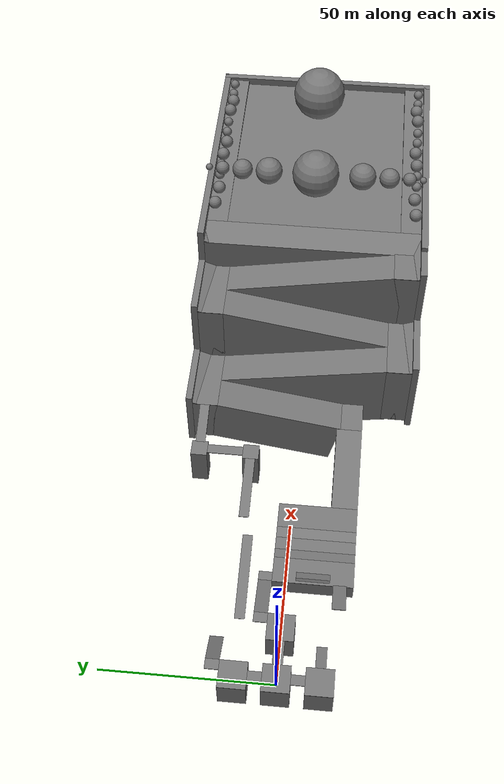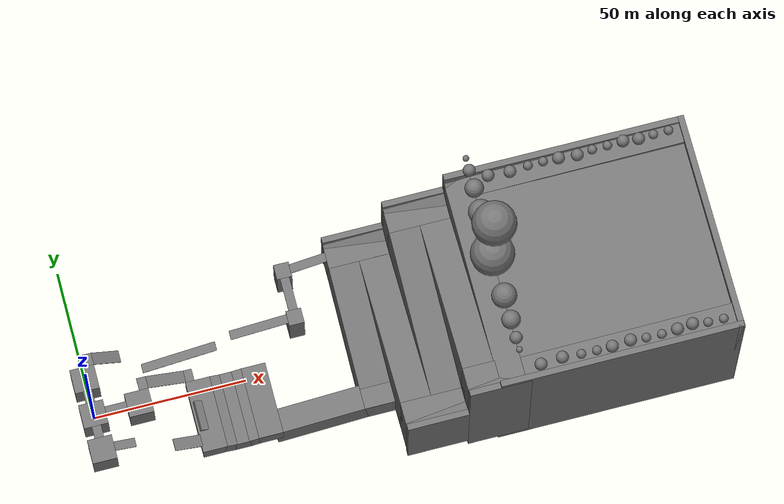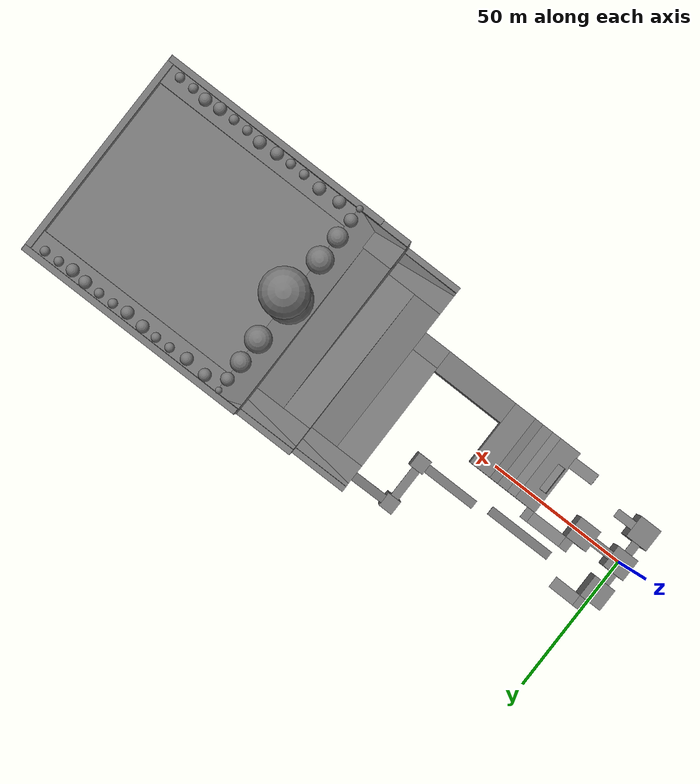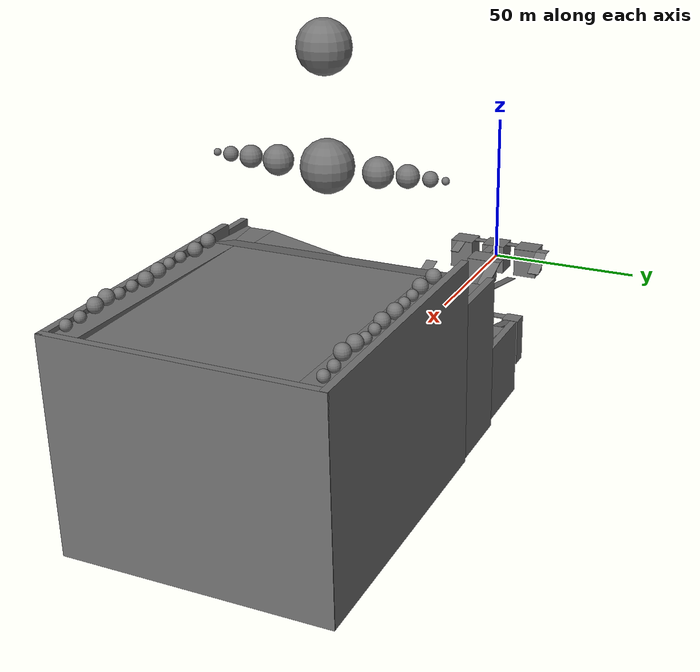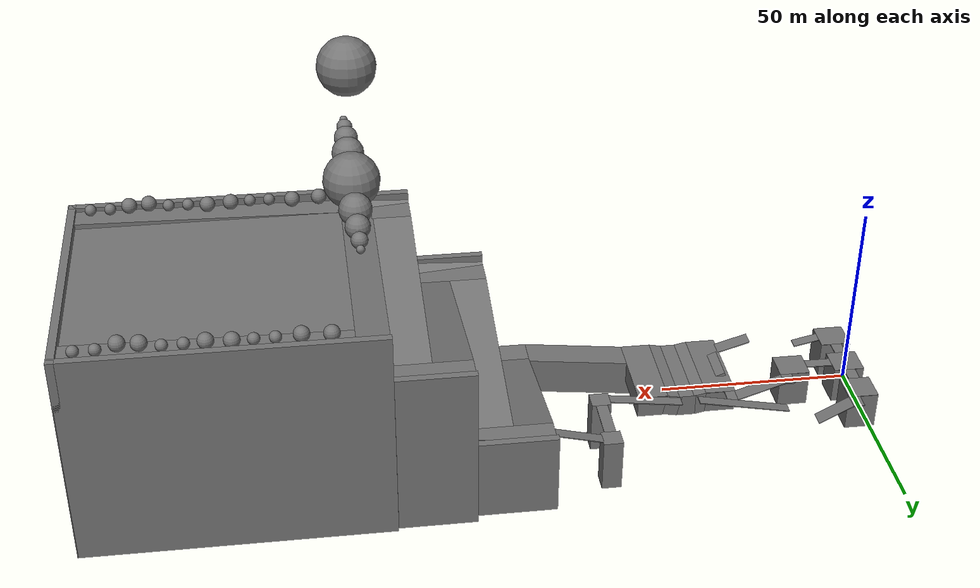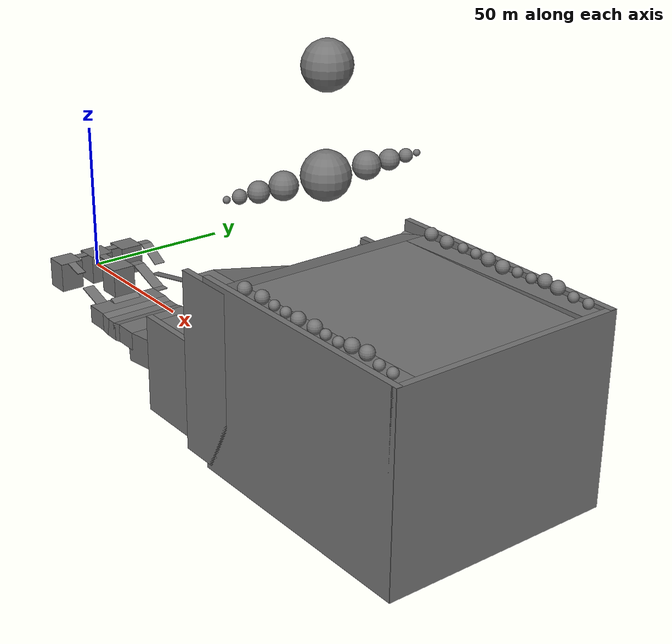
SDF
<sdf version="1.10">
 <world name="waterworld">
  <physics name="ode_cpu" type="ode">
   <max_step_size>0.002</max_step_size>
   <real_time_update_rate>500</real_time_update_rate>
   <real_time_factor>1.0</real_time_factor>
   <ode>
    <solver><type>quick</type><iters>50</iters><sor>1.3</sor></solver>
    <constraints><cfm>0.0</cfm><erp>0.2</erp></constraints>
   </ode>
  </physics>
  <plugin name="gz::sim::systems::Physics" filename="gz-sim-physics-system"/>
  <plugin name="gz::sim::systems::UserCommands" filename="gz-sim-user-commands-system"/>
  <plugin name="gz::sim::systems::SceneBroadcaster" filename="gz-sim-scene-broadcaster-system"/>
  <plugin name="gz::sim::systems::Contact" filename="gz-sim-contact-system"/>
  <gravity>0 0 -9.81</gravity>
  <magnetic_field>5.5644999999999998e-06 2.2875799999999999e-05 -4.2388400000000002e-05</magnetic_field>
  <atmosphere type="adiabatic"/>
  <scene><ambient>0.5 0.5 0.5 1</ambient><background>0.7 0.7 0.75 1</background><shadows>false</shadows></scene>
  <model name="central_tower">
   <static>true</static>
   <link name="link">
    <collision name="col"><geometry><box><size>8 8 10</size></box></geometry></collision>
    <visual name="vis">
     <geometry><box><size>8 8 10</size></box></geometry>
     <material>
      <ambient>0.35 0.35 0.35 1</ambient>
      <diffuse>0.45 0.45 0.45 1</diffuse>
      <pbr>
       <metal>
        <albedo_map>model://textures/stone_textures/stone_wall_seamless_1x1.jpg</albedo_map>
        <roughness>0.9</roughness>
        <metalness>0.0</metalness>
       </metal>
      </pbr>
     </material>
    </visual>
   </link>
  </model>
  <model name="central_arena_floor_model">
   <static>true</static>
   <pose>0 0 5 0 0 0</pose>
   <link name="central_arena_floor_link">
    <collision name="col">
     <geometry><box><size>8 8 0.1</size></box></geometry>
     <surface>
      <friction><ode><mu>0.9</mu><mu2>0.9</mu2><fdir1>1 0 0</fdir1></ode></friction>
      <bounce><restitution_coefficient>0.03</restitution_coefficient><threshold>1e3</threshold></bounce>
      <contact><ode><kp>1e6</kp><kd>1e3</kd><max_vel>1.0</max_vel><min_depth>0.001</min_depth></ode></contact>
     </surface>
    </collision>
    <visual name="vis">
     <geometry><box><size>8 8 0.1</size></box></geometry>
     <material>
      <ambient>0.35 0.35 0.35 1</ambient>
      <diffuse>0.45 0.45 0.45 1</diffuse>
      <pbr>
       <metal>
        <albedo_map>model://textures/grass_textures/green_grass_seamless.jpg</albedo_map>
        <roughness>0.9</roughness>
        <metalness>0.0</metalness>
       </metal>
      </pbr>
     </material>
    </visual>
   </link>
  </model>
  <model name="west_tower">
   <static>true</static>
   <link name="link">
    <pose>0 12 0 0 0 0</pose>
    <collision name="col"><geometry><box><size>8 8 10</size></box></geometry></collision>
    <visual name="vis">
     <geometry><box><size>8 8 10</size></box></geometry>
     <material>
      <ambient>0.35 0.35 0.35 1</ambient>
      <diffuse>0.45 0.45 0.45 1</diffuse>
      <pbr>
       <metal>
        <albedo_map>model://textures/stone_textures/stone_wall_seamless_1x1.jpg</albedo_map>
        <roughness>0.9</roughness>
        <metalness>0.0</metalness>
       </metal>
      </pbr>
     </material>
    </visual>
   </link>
  </model>
  <model name="west_arena_floor_model">
   <static>true</static>
   <pose>0 12 5 0 0 0</pose>
   <link name="west_arena_floor_link">
    <collision name="col">
     <geometry><box><size>8 8 0.1</size></box></geometry>
     <surface>
      <friction><ode><mu>0.9</mu><mu2>0.9</mu2><fdir1>1 0 0</fdir1></ode></friction>
      <bounce><restitution_coefficient>0.03</restitution_coefficient><threshold>1e3</threshold></bounce>
      <contact><ode><kp>1e6</kp><kd>1e3</kd><max_vel>1.0</max_vel><min_depth>0.001</min_depth></ode></contact>
     </surface>
    </collision>
    <visual name="vis">
     <geometry><box><size>8 8 0.1</size></box></geometry>
     <material>
      <ambient>0.35 0.35 0.35 1</ambient>
      <diffuse>0.45 0.45 0.45 1</diffuse>
      <pbr>
       <metal>
        <albedo_map>model://textures/grass_textures/green_grass_seamless.jpg</albedo_map>
        <roughness>0.9</roughness>
        <metalness>0.0</metalness>
       </metal>
      </pbr>
     </material>
    </visual>
   </link>
  </model>
  <model name="east_tower">
   <static>true</static>
   <link name="link">
    <pose>0 -12 0 0 0 0</pose>
    <collision name="col"><geometry><box><size>8 8 10</size></box></geometry></collision>
    <visual name="vis">
     <geometry><box><size>8 8 10</size></box></geometry>
     <material>
      <ambient>0.35 0.35 0.35 1</ambient>
      <diffuse>0.45 0.45 0.45 1</diffuse>
      <pbr>
       <metal>
        <albedo_map>model://textures/stone_textures/stone_wall_seamless_1x1.jpg</albedo_map>
        <roughness>0.9</roughness>
        <metalness>0.0</metalness>
       </metal>
      </pbr>
     </material>
    </visual>
   </link>
  </model>
  <model name="east_arena_floor_model">
   <static>true</static>
   <pose>0 -12 5 0 0 0</pose>
   <link name="east_arena_floor_link">
    <collision name="col">
     <geometry><box><size>8 8 0.1</size></box></geometry>
     <surface>
      <friction><ode><mu>0.9</mu><mu2>0.9</mu2><fdir1>1 0 0</fdir1></ode></friction>
      <bounce><restitution_coefficient>0.03</restitution_coefficient><threshold>1e3</threshold></bounce>
      <contact><ode><kp>1e6</kp><kd>1e3</kd><max_vel>1.0</max_vel><min_depth>0.001</min_depth></ode></contact>
     </surface>
    </collision>
    <visual name="vis">
     <geometry><box><size>8 8 0.1</size></box></geometry>
     <material>
      <ambient>0.35 0.35 0.35 1</ambient>
      <diffuse>0.45 0.45 0.45 1</diffuse>
      <pbr>
       <metal>
        <albedo_map>model://textures/grass_textures/green_grass_seamless.jpg</albedo_map>
        <roughness>0.9</roughness>
        <metalness>0.0</metalness>
       </metal>
      </pbr>
     </material>
    </visual>
   </link>
  </model>
  <model name="north_tower">
   <static>true</static>
   <link name="link">
    <pose>15 0 0 0 0 0</pose>
    <collision name="col"><geometry><box><size>8 8 10</size></box></geometry></collision>
    <visual name="vis">
     <geometry><box><size>8 8 10</size></box></geometry>
     <material>
      <ambient>0.35 0.35 0.35 1</ambient>
      <diffuse>0.45 0.45 0.45 1</diffuse>
      <pbr>
       <metal>
        <albedo_map>model://textures/stone_textures/stone_wall_seamless_1x1.jpg</albedo_map>
        <roughness>0.9</roughness>
        <metalness>0.0</metalness>
       </metal>
      </pbr>
     </material>
    </visual>
   </link>
  </model>
  <model name="north_arena_floor_model">
   <static>true</static>
   <pose>15 0 5 0 0 0</pose>
   <link name="north_arena_floor_link">
    <collision name="col">
     <geometry><box><size>8 8 0.1</size></box></geometry>
     <surface>
      <friction><ode><mu>0.9</mu><mu2>0.9</mu2><fdir1>1 0 0</fdir1></ode></friction>
      <bounce><restitution_coefficient>0.03</restitution_coefficient><threshold>1e3</threshold></bounce>
      <contact><ode><kp>1e6</kp><kd>1e3</kd><max_vel>1.0</max_vel><min_depth>0.001</min_depth></ode></contact>
     </surface>
    </collision>
    <visual name="vis">
     <geometry><box><size>8 8 0.1</size></box></geometry>
     <material>
      <ambient>0.35 0.35 0.35 1</ambient>
      <diffuse>0.45 0.45 0.45 1</diffuse>
      <pbr>
       <metal>
        <albedo_map>model://textures/grass_textures/green_grass_seamless.jpg</albedo_map>
        <roughness>0.9</roughness>
        <metalness>0.0</metalness>
       </metal>
      </pbr>
     </material>
    </visual>
   </link>
  </model>
  <model name="tidal_island_segment_1">
   <static>true</static>
   <link name="link">
    <pose>35 -8 -2.2 0 0 0</pose>
    <collision name="col"><geometry><box><size>8 24 6</size></box></geometry></collision>
    <visual name="vis">
     <geometry><box><size>8 24 6</size></box></geometry>
     <material>
      <ambient>0.35 0.35 0.35 1</ambient>
      <diffuse>0.45 0.45 0.45 1</diffuse>
      <pbr>
       <metal>
        <albedo_map>model://textures/stone_textures/stone_wall_seamless_1x1.jpg</albedo_map>
        <roughness>0.9</roughness>
        <metalness>0.0</metalness>
       </metal>
      </pbr>
     </material>
    </visual>
   </link>
  </model>
  <model name="tidal_island_segment_1_ramp">
   <static>true</static>
   <link name="link">
    <pose>33 -8 -0.1 0 0.4 0</pose>
    <collision name="col"><geometry><box><size>3 10 3</size></box></geometry></collision>
    <visual name="vis">
     <geometry><box><size>3 10 3</size></box></geometry>
     <material>
      <ambient>0.35 0.35 0.35 1</ambient>
      <diffuse>0.45 0.45 0.45 1</diffuse>
      <pbr>
       <metal>
        <albedo_map>model://textures/stone_textures/stone_wall_seamless_1x1.jpg</albedo_map>
        <roughness>0.9</roughness>
        <metalness>0.0</metalness>
       </metal>
      </pbr>
     </material>
    </visual>
   </link>
  </model>
  <model name="tidal_island_segment_1_floor_model">
   <static>true</static>
   <pose>35 -8 0.8 0 0 0</pose>
   <link name="north_arena_floor_link">
    <collision name="col">
     <geometry><box><size>8 24 0.1</size></box></geometry>
     <surface>
      <friction><ode><mu>0.9</mu><mu2>0.9</mu2><fdir1>1 0 0</fdir1></ode></friction>
      <bounce><restitution_coefficient>0.03</restitution_coefficient><threshold>1e3</threshold></bounce>
      <contact><ode><kp>1e6</kp><kd>1e3</kd><max_vel>1.0</max_vel><min_depth>0.001</min_depth></ode></contact>
     </surface>
    </collision>
    <visual name="vis">
     <geometry><box><size>8 24 0.1</size></box></geometry>
     <material>
      <ambient>0.35 0.35 0.35 1</ambient>
      <diffuse>0.45 0.45 0.45 1</diffuse>
      <pbr>
       <metal>
        <albedo_map>model://textures/grass_textures/green_grass_seamless.jpg</albedo_map>
        <roughness>0.9</roughness>
        <metalness>0.0</metalness>
       </metal>
      </pbr>
     </material>
    </visual>
   </link>
  </model>
  <model name="tidal_island_segment_2">
   <static>true</static>
   <link name="link">
    <pose>40.3641 -8 -2.4876 0 0.2 0</pose>
    <collision name="col"><geometry><box><size>4 24 6</size></box></geometry></collision>
    <visual name="vis">
     <geometry><box><size>4 24 6</size></box></geometry>
     <material>
      <ambient>0.35 0.35 0.35 1</ambient>
      <diffuse>0.45 0.45 0.45 1</diffuse>
      <pbr>
       <metal>
        <albedo_map>model://textures/stone_textures/stone_wall_seamless_4x1.jpg</albedo_map>
        <roughness>0.9</roughness>
        <metalness>0.0</metalness>
       </metal>
      </pbr>
     </material>
    </visual>
   </link>
  </model>
  <model name="tidal_island_segment_3">
   <static>true</static>
   <link name="link">
    <pose>44.2 -8 -2.8 0 0 0</pose>
    <collision name="col"><geometry><box><size>5 24 6</size></box></geometry></collision>
    <visual name="vis">
     <geometry><box><size>5 24 6</size></box></geometry>
     <material>
      <ambient>0.35 0.35 0.35 1</ambient>
      <diffuse>0.45 0.45 0.45 1</diffuse>
      <pbr>
       <metal>
        <albedo_map>model://textures/stone_textures/stone_wall_seamless_4x1.jpg</albedo_map>
        <roughness>0.9</roughness>
        <metalness>0.0</metalness>
       </metal>
      </pbr>
     </material>
    </visual>
   </link>
  </model>
  <model name="tidal_island_segment_4">
   <static>true</static>
   <link name="link">
    <pose>48 -8 -2.4876 0 -0.2 0</pose>
    <collision name="col"><geometry><box><size>4 24 6</size></box></geometry></collision>
    <visual name="vis">
     <geometry><box><size>4 24 6</size></box></geometry>
     <material>
      <ambient>0.35 0.35 0.35 1</ambient>
      <diffuse>0.45 0.45 0.45 1</diffuse>
      <pbr>
       <metal>
        <albedo_map>model://textures/stone_textures/stone_wall_seamless_4x1.jpg</albedo_map>
        <roughness>0.9</roughness>
        <metalness>0.0</metalness>
       </metal>
      </pbr>
     </material>
    </visual>
   </link>
  </model>
  <model name="tidal_island_segment_5">
   <static>true</static>
   <link name="link">
    <pose>53.3641 -8 -2.2 0 0 0</pose>
    <collision name="col"><geometry><box><size>8 24 6</size></box></geometry></collision>
    <visual name="vis">
     <geometry><box><size>8 24 6</size></box></geometry>
     <material>
      <ambient>0.35 0.35 0.35 1</ambient>
      <diffuse>0.45 0.45 0.45 1</diffuse>
      <pbr>
       <metal>
        <albedo_map>model://textures/stone_textures/stone_wall_seamless_1x1.jpg</albedo_map>
        <roughness>0.9</roughness>
        <metalness>0.0</metalness>
       </metal>
      </pbr>
     </material>
    </visual>
   </link>
  </model>
  <model name="tidal_island_segment_5_floor_model">
   <static>true</static>
   <pose>53.3641 -8 0.7999 0 0 0</pose>
   <link name="north_arena_floor_link">
    <collision name="col">
     <geometry><box><size>8 24 0.1</size></box></geometry>
     <surface>
      <friction><ode><mu>0.9</mu><mu2>0.9</mu2><fdir1>1 0 0</fdir1></ode></friction>
      <bounce><restitution_coefficient>0.03</restitution_coefficient><threshold>1e3</threshold></bounce>
      <contact><ode><kp>1e6</kp><kd>1e3</kd><max_vel>1.0</max_vel><min_depth>0.001</min_depth></ode></contact>
     </surface>
    </collision>
    <visual name="vis">
     <geometry><box><size>8 24 0.1</size></box></geometry>
     <material>
      <ambient>0.35 0.35 0.35 1</ambient>
      <diffuse>0.45 0.45 0.45 1</diffuse>
      <pbr>
       <metal>
        <albedo_map>model://textures/grass_textures/green_grass_seamless.jpg</albedo_map>
        <roughness>0.9</roughness>
        <metalness>0.0</metalness>
       </metal>
      </pbr>
     </material>
    </visual>
   </link>
  </model>
  <model name="north_bridge">
   <static>true</static>
   <link name="link">
    <pose>7.5 0 4.925 0 0 0</pose>
    <collision name="col"><geometry><box><size>7 3 0.25</size></box></geometry></collision>
    <visual name="vis">
     <geometry><box><size>7 3 0.25</size></box></geometry>
     <material>
      <ambient>0.35 0.35 0.35 1</ambient>
      <diffuse>0.45 0.45 0.45 1</diffuse>
      <pbr>
       <metal>
        <albedo_map>model://textures/wood_textures/wood_texture_seamless_1x2.jpg</albedo_map>
        <roughness>0.9</roughness>
        <metalness>0.0</metalness>
       </metal>
      </pbr>
     </material>
    </visual>
   </link>
  </model>
  <model name="east_bridge">
   <static>true</static>
   <link name="link">
    <pose>0 -6 4.925 0 0 0</pose>
    <collision name="col"><geometry><box><size>3 4 0.25</size></box></geometry></collision>
    <visual name="vis">
     <geometry><box><size>3 4 0.25</size></box></geometry>
     <material>
      <ambient>0.35 0.35 0.35 1</ambient>
      <diffuse>0.45 0.45 0.45 1</diffuse>
      <pbr>
       <metal>
        <albedo_map>model://textures/wood_textures/wood_texture_seamless_1x1.jpg</albedo_map>
        <roughness>0.9</roughness>
        <metalness>0.0</metalness>
       </metal>
      </pbr>
     </material>
    </visual>
   </link>
  </model>
  <model name="west_bridge">
   <static>true</static>
   <link name="link">
    <pose>0 6 4.925 0 0 0</pose>
    <collision name="col"><geometry><box><size>3 4 0.25</size></box></geometry></collision>
    <visual name="vis">
     <geometry><box><size>3 4 0.25</size></box></geometry>
     <material>
      <ambient>0.35 0.35 0.35 1</ambient>
      <diffuse>0.45 0.45 0.45 1</diffuse>
      <pbr>
       <metal>
        <albedo_map>model://textures/wood_textures/wood_texture_seamless_1x1.jpg</albedo_map>
        <roughness>0.9</roughness>
        <metalness>0.0</metalness>
       </metal>
      </pbr>
     </material>
    </visual>
   </link>
  </model>
  <model name="east_north_bridge">
   <static>true</static>
   <link name="link">
    <pose>7.39 -12 4.165 0 0.22 0</pose>
    <collision name="col"><geometry><box><size>7 3 0.25</size></box></geometry></collision>
    <visual name="vis">
     <geometry><box><size>7 3 0.25</size></box></geometry>
     <material>
      <ambient>0.35 0.35 0.35 1</ambient>
      <diffuse>0.45 0.45 0.45 1</diffuse>
      <pbr>
       <metal>
        <albedo_map>model://textures/wood_textures/wood_texture_seamless_1x2.jpg</albedo_map>
        <roughness>0.9</roughness>
        <metalness>0.0</metalness>
       </metal>
      </pbr>
     </material>
    </visual>
   </link>
  </model>
  <model name="west_north_bridge_platform">
   <static>true</static>
   <link name="link">
    <pose>2.5 18 4.925 0 0 0</pose>
    <collision name="col"><geometry><box><size>3 4 0.25</size></box></geometry></collision>
    <visual name="vis">
     <geometry><box><size>3 4 0.25</size></box></geometry>
     <material>
      <ambient>0.35 0.35 0.35 1</ambient>
      <diffuse>0.45 0.45 0.45 1</diffuse>
      <pbr>
       <metal>
        <albedo_map>model://textures/wood_textures/wood_texture_seamless_1x1.jpg</albedo_map>
        <roughness>0.9</roughness>
        <metalness>0.0</metalness>
       </metal>
      </pbr>
     </material>
    </visual>
   </link>
  </model>
  <model name="west_north_bridge">
   <static>true</static>
   <link name="link">
    <pose>8.328 18 2.543 0 0.5 0</pose>
    <collision name="col"><geometry><box><size>10 4 0.25</size></box></geometry></collision>
    <visual name="vis">
     <geometry><box><size>10 4 0.25</size></box></geometry>
     <material>
      <ambient>0.35 0.35 0.35 1</ambient>
      <diffuse>0.45 0.45 0.45 1</diffuse>
      <pbr>
       <metal>
        <albedo_map>model://textures/wood_textures/wood_texture_seamless_1x3.jpg</albedo_map>
        <roughness>0.9</roughness>
        <metalness>0.0</metalness>
       </metal>
      </pbr>
     </material>
    </visual>
   </link>
  </model>
  <model name="west_north_north_bridge">
   <static>true</static>
   <link name="link">
    <pose>31 12.2 2.5 0 -0.2 0</pose>
    <collision name="col"><geometry><box><size>25 3 0.25</size></box></geometry></collision>
    <visual name="vis">
     <geometry><box><size>25 3 0.25</size></box></geometry>
     <material>
      <ambient>0.35 0.35 0.35 1</ambient>
      <diffuse>0.45 0.45 0.45 1</diffuse>
      <pbr>
       <metal>
        <albedo_map>model://textures/wood_textures/wood_texture_seamless_1x10.jpg</albedo_map>
        <roughness>0.9</roughness>
        <metalness>0.0</metalness>
       </metal>
      </pbr>
     </material>
    </visual>
   </link>
  </model>
  <model name="north_north_bridge_platform_1">
   <static>true</static>
   <link name="link">
    <pose>17.5 6 4.925 0 0 0</pose>
    <collision name="col"><geometry><box><size>3 4 0.25</size></box></geometry></collision>
    <visual name="vis">
     <geometry><box><size>3 4 0.25</size></box></geometry>
     <material>
      <ambient>0.35 0.35 0.35 1</ambient>
      <diffuse>0.45 0.45 0.45 1</diffuse>
      <pbr>
       <metal>
        <albedo_map>model://textures/wood_textures/wood_texture_seamless_1x3.jpg</albedo_map>
        <roughness>0.9</roughness>
        <metalness>0.0</metalness>
       </metal>
      </pbr>
     </material>
    </visual>
   </link>
  </model>
  <model name="north_north_bridge">
   <static>true</static>
   <link name="link">
    <pose>25.1 6 2.82 0 0.33 0</pose>
    <collision name="col"><geometry><box><size>13 4 0.25</size></box></geometry></collision>
    <visual name="vis">
     <geometry><box><size>13 4 0.25</size></box></geometry>
     <material>
      <ambient>0.35 0.35 0.35 1</ambient>
      <diffuse>0.45 0.45 0.45 1</diffuse>
      <pbr>
       <metal>
        <albedo_map>model://textures/wood_textures/wood_texture_seamless_1x3.jpg</albedo_map>
        <roughness>0.9</roughness>
        <metalness>0.0</metalness>
       </metal>
      </pbr>
     </material>
    </visual>
   </link>
  </model>
  <model name="north_north_bridge_platform_2">
   <static>true</static>
   <link name="link">
    <pose>32.5 6 0.725 0 0 0</pose>
    <collision name="col"><geometry><box><size>3 4 0.25</size></box></geometry></collision>
    <visual name="vis">
     <geometry><box><size>3 4 0.25</size></box></geometry>
     <material>
      <ambient>0.35 0.35 0.35 1</ambient>
      <diffuse>0.45 0.45 0.45 1</diffuse>
      <pbr>
       <metal>
        <albedo_map>model://textures/wood_textures/wood_texture_seamless_1x1.jpg</albedo_map>
        <roughness>0.9</roughness>
        <metalness>0.0</metalness>
       </metal>
      </pbr>
     </material>
    </visual>
   </link>
  </model>
  <model name="east_north_north_bridge">
   <static>true</static>
   <link name="link">
    <pose>27.26 -16 1.986 0 0.3 0</pose>
    <collision name="col"><geometry><box><size>10 4 0.25</size></box></geometry></collision>
    <visual name="vis">
     <geometry><box><size>10 4 0.25</size></box></geometry>
     <material>
      <ambient>0.35 0.35 0.35 1</ambient>
      <diffuse>0.45 0.45 0.45 1</diffuse>
      <pbr>
       <metal>
        <albedo_map>model://textures/wood_textures/wood_texture_seamless_1x5.jpg</albedo_map>
        <roughness>0.9</roughness>
        <metalness>0.0</metalness>
       </metal>
      </pbr>
     </material>
    </visual>
   </link>
  </model>
  <model name="stone_bridge_1">
   <static>true</static>
   <link name="link">
    <pose>70 -15.999 -2.66 0 -0.12 0</pose>
    <collision name="col"><geometry><box><size>30 8 10</size></box></geometry></collision>
    <visual name="vis">
     <geometry><box><size>30 8 10</size></box></geometry>
     <material>
      <ambient>0.35 0.35 0.35 1</ambient>
      <diffuse>0.45 0.45 0.45 1</diffuse>
      <pbr>
       <metal>
        <albedo_map>model://textures/stone_textures/stone_wall_seamless_1x3.jpg</albedo_map>
        <roughness>0.9</roughness>
        <metalness>0.0</metalness>
       </metal>
      </pbr>
     </material>
    </visual>
   </link>
  </model>
  <model name="east_north_north_north_bridge_1">
   <static>true</static>
   <link name="link">
    <pose>57.978 14 7.6 0 -0.133 0</pose>
    <collision name="col"><geometry><box><size>19.25 3 0.25</size></box></geometry></collision>
    <visual name="vis">
     <geometry><box><size>19.25 3 0.25</size></box></geometry>
     <material>
      <ambient>0.35 0.35 0.35 1</ambient>
      <diffuse>0.45 0.45 0.45 1</diffuse>
      <pbr>
       <metal>
        <albedo_map>model://textures/wood_textures/wood_texture_seamless_1x5.jpg</albedo_map>
        <roughness>0.9</roughness>
        <metalness>0.0</metalness>
       </metal>
      </pbr>
     </material>
    </visual>
   </link>
  </model>
  <model name="east_north_north_north_bridge_platform_1">
   <static>true</static>
   <link name="link">
    <pose>70 14 2 0 0 0</pose>
    <collision name="col"><geometry><box><size>5 5 14</size></box></geometry></collision>
    <visual name="vis">
     <geometry><box><size>5 5 14</size></box></geometry>
     <material>
      <ambient>0.35 0.35 0.35 1</ambient>
      <diffuse>0.45 0.45 0.45 1</diffuse>
      <pbr>
       <metal>
        <albedo_map>model://textures/stone_textures/stone_wall_seamless_1x1.jpg</albedo_map>
        <roughness>0.9</roughness>
        <metalness>0.0</metalness>
       </metal>
      </pbr>
     </material>
    </visual>
   </link>
  </model>
  <model name="east_north_north_north_bridge_2">
   <static>true</static>
   <link name="link">
    <pose>70 22 8.875 0 0 0</pose>
    <collision name="col"><geometry><box><size>3 11 0.25</size></box></geometry></collision>
    <visual name="vis">
     <geometry><box><size>3 11 0.25</size></box></geometry>
     <material>
      <ambient>0.35 0.35 0.35 1</ambient>
      <diffuse>0.45 0.45 0.45 1</diffuse>
      <pbr>
       <metal>
        <albedo_map>model://textures/wood_textures/wood_texture_seamless_1x1.jpg</albedo_map>
        <roughness>0.9</roughness>
        <metalness>0.0</metalness>
       </metal>
      </pbr>
     </material>
    </visual>
   </link>
  </model>
  <model name="east_north_north_north_bridge_platform_2">
   <static>true</static>
   <link name="link">
    <pose>70 30 2 0 0 0</pose>
    <collision name="col"><geometry><box><size>5 5 14</size></box></geometry></collision>
    <visual name="vis">
     <geometry><box><size>5 5 14</size></box></geometry>
     <material>
      <ambient>0.35 0.35 0.35 1</ambient>
      <diffuse>0.45 0.45 0.45 1</diffuse>
      <pbr>
       <metal>
        <albedo_map>model://textures/stone_textures/stone_wall_seamless_1x1.jpg</albedo_map>
        <roughness>0.9</roughness>
        <metalness>0.0</metalness>
       </metal>
      </pbr>
     </material>
    </visual>
   </link>
  </model>
  <model name="east_north_north_north_bridge_3">
   <static>true</static>
   <link name="link">
    <pose>78.265 30 10.385 0 -0.25 0</pose>
    <collision name="col"><geometry><box><size>12.5 3 0.25</size></box></geometry></collision>
    <visual name="vis">
     <geometry><box><size>12.5 3 0.25</size></box></geometry>
     <material>
      <ambient>0.35 0.35 0.35 1</ambient>
      <diffuse>0.45 0.45 0.45 1</diffuse>
      <pbr>
       <metal>
        <albedo_map>model://textures/wood_textures/wood_texture_seamless_1x5.jpg</albedo_map>
        <roughness>0.9</roughness>
        <metalness>0.0</metalness>
       </metal>
      </pbr>
     </material>
    </visual>
   </link>
  </model>
  <model name="ramp_tower_left_landing_1">
   <static>true</static>
   <link name="link">
    <pose>94.29 30 3.5 0 0 0</pose>
    <collision name="col"><geometry><box><size>20 8 17</size></box></geometry></collision>
    <visual name="vis">
     <geometry><box><size>20 8 17</size></box></geometry>
     <material>
      <ambient>0.35 0.35 0.35 1</ambient>
      <diffuse>0.45 0.45 0.45 1</diffuse>
      <pbr>
       <metal>
        <albedo_map>model://textures/stone_textures/stone_wall_seamless_1x1.jpg</albedo_map>
        <roughness>0.9</roughness>
        <metalness>0.0</metalness>
       </metal>
      </pbr>
     </material>
    </visual>
   </link>
  </model>
  <model name="ramp_tower_left_landing_1_floor">
   <static>true</static>
   <pose>94.29 30 12 0 0 0</pose>
   <link name="west_arena_floor_link">
    <collision name="col">
     <geometry><box><size>20 8 0.1</size></box></geometry>
     <surface>
      <friction><ode><mu>0.9</mu><mu2>0.9</mu2><fdir1>1 0 0</fdir1></ode></friction>
      <bounce><restitution_coefficient>0.03</restitution_coefficient><threshold>1e3</threshold></bounce>
      <contact><ode><kp>1e6</kp><kd>1e3</kd><max_vel>1.0</max_vel><min_depth>0.001</min_depth></ode></contact>
     </surface>
    </collision>
    <visual name="vis">
     <geometry><box><size>20 8 0.1</size></box></geometry>
     <material>
      <ambient>0.35 0.35 0.35 1</ambient>
      <diffuse>0.45 0.45 0.45 1</diffuse>
      <pbr>
       <metal>
        <albedo_map>model://textures/grass_textures/green_grass_seamless.jpg</albedo_map>
        <roughness>0.9</roughness>
        <metalness>0.0</metalness>
       </metal>
      </pbr>
     </material>
    </visual>
   </link>
  </model>
  <model name="ramp_tower_left_landing_1_wall">
   <static>true</static>
   <link name="link">
    <pose>94.29 35 3.5 0 0 0</pose>
    <collision name="col"><geometry><box><size>20 2 22</size></box></geometry></collision>
    <visual name="vis">
     <geometry><box><size>20 2 22</size></box></geometry>
     <material>
      <ambient>0.35 0.35 0.35 1</ambient>
      <diffuse>0.45 0.45 0.45 1</diffuse>
      <pbr>
       <metal>
        <albedo_map>model://textures/stone_textures/stone_wall_seamless_1x1.jpg</albedo_map>
        <roughness>0.9</roughness>
        <metalness>0.0</metalness>
       </metal>
      </pbr>
     </material>
    </visual>
   </link>
  </model>
  <model name="ramp_tower_left_landing_1_ramp">
   <static>true</static>
   <link name="link">
    <pose>94.6 33 11 0.40 -0.05 0</pose>
    <collision name="col"><geometry><box><size>20.4 5 3</size></box></geometry></collision>
    <visual name="vis">
     <geometry><box><size>20.4 5 3</size></box></geometry>
     <material>
      <ambient>0.35 0.35 0.35 1</ambient>
      <diffuse>0.45 0.45 0.45 1</diffuse>
      <pbr>
       <metal>
        <albedo_map>model://textures/stone_textures/stone_wall_seamless_1x1.jpg</albedo_map>
        <roughness>0.9</roughness>
        <metalness>0.0</metalness>
       </metal>
      </pbr>
     </material>
    </visual>
   </link>
  </model>
  <model name="ramp_tower_right_landing_1">
   <static>true</static>
   <link name="link">
    <pose>89.29 -15.999 -0.95 0 0 0</pose>
    <collision name="col"><geometry><box><size>10 8 10</size></box></geometry></collision>
    <visual name="vis">
     <geometry><box><size>10 8 10</size></box></geometry>
     <material>
      <ambient>0.35 0.35 0.35 1</ambient>
      <diffuse>0.45 0.45 0.45 1</diffuse>
      <pbr>
       <metal>
        <albedo_map>model://textures/stone_textures/stone_wall_seamless_1x1.jpg</albedo_map>
        <roughness>0.9</roughness>
        <metalness>0.0</metalness>
       </metal>
      </pbr>
     </material>
    </visual>
   </link>
  </model>
  <model name="ramp_tower_right_landing_1_floor">
   <static>true</static>
   <pose>89.29 -15.999 4.05 0 0 0</pose>
   <link name="west_arena_floor_link">
    <collision name="col">
     <geometry><box><size>10 8 0.1</size></box></geometry>
     <surface>
      <friction><ode><mu>0.9</mu><mu2>0.9</mu2><fdir1>1 0 0</fdir1></ode></friction>
      <bounce><restitution_coefficient>0.03</restitution_coefficient><threshold>1e3</threshold></bounce>
      <contact><ode><kp>1e6</kp><kd>1e3</kd><max_vel>1.0</max_vel><min_depth>0.001</min_depth></ode></contact>
     </surface>
    </collision>
    <visual name="vis">
     <geometry><box><size>10 8 0.1</size></box></geometry>
     <material>
      <ambient>0.35 0.35 0.35 1</ambient>
      <diffuse>0.45 0.45 0.45 1</diffuse>
      <pbr>
       <metal>
        <albedo_map>model://textures/grass_textures/green_grass_seamless.jpg</albedo_map>
        <roughness>0.9</roughness>
        <metalness>0.0</metalness>
       </metal>
      </pbr>
     </material>
    </visual>
   </link>
  </model>
  <model name="ramp_tower_ramp_1">
   <static>true</static>
   <link name="link">
    <pose>89.29 8.087 -0.253 0.2 0 0</pose>
    <collision name="col"><geometry><box><size>10 40 17</size></box></geometry></collision>
    <visual name="vis">
     <geometry><box><size>10 40 17</size></box></geometry>
     <material>
      <ambient>0.35 0.35 0.35 1</ambient>
      <diffuse>0.45 0.45 0.45 1</diffuse>
      <pbr>
       <metal>
        <albedo_map>model://textures/stone_textures/stone_wall_seamless_4x1.jpg</albedo_map>
        <roughness>0.9</roughness>
        <metalness>0.0</metalness>
       </metal>
      </pbr>
     </material>
    </visual>
   </link>
  </model>
  <model name="ramp_tower_ramp_2">
   <static>true</static>
   <link name="link">
    <pose>99.29 0 4.55 -0.2 0 0</pose>
    <collision name="col"><geometry><box><size>10 58.15 25</size></box></geometry></collision>
    <visual name="vis">
     <geometry><box><size>10 58.15 25</size></box></geometry>
     <material>
      <ambient>0.35 0.35 0.35 1</ambient>
      <diffuse>0.45 0.45 0.45 1</diffuse>
      <pbr>
       <metal>
        <albedo_map>model://textures/stone_textures/stone_wall_seamless_4x1.jpg</albedo_map>
        <roughness>0.9</roughness>
        <metalness>0.0</metalness>
       </metal>
      </pbr>
     </material>
    </visual>
   </link>
  </model>
  <model name="ramp_tower_left_landing_2">
   <static>true</static>
   <link name="link">
    <pose>104.29 -30 10 0 0 0</pose>
    <collision name="col"><geometry><box><size>20 8 25</size></box></geometry></collision>
    <visual name="vis">
     <geometry><box><size>20 8 25</size></box></geometry>
     <material>
      <ambient>0.35 0.35 0.35 1</ambient>
      <diffuse>0.45 0.45 0.45 1</diffuse>
      <pbr>
       <metal>
        <albedo_map>model://textures/stone_textures/stone_wall_seamless_1x1.jpg</albedo_map>
        <roughness>0.9</roughness>
        <metalness>0.0</metalness>
       </metal>
      </pbr>
     </material>
    </visual>
   </link>
  </model>
  <model name="ramp_tower_left_landing_2_floor">
   <static>true</static>
   <pose>104.29 -30 22.524 0 0 0</pose>
   <link name="west_arena_floor_link">
    <collision name="col">
     <geometry><box><size>20 8 0.1</size></box></geometry>
     <surface>
      <friction><ode><mu>0.9</mu><mu2>0.9</mu2><fdir1>1 0 0</fdir1></ode></friction>
      <bounce><restitution_coefficient>0.03</restitution_coefficient><threshold>1e3</threshold></bounce>
      <contact><ode><kp>1e6</kp><kd>1e3</kd><max_vel>1.0</max_vel><min_depth>0.001</min_depth></ode></contact>
     </surface>
    </collision>
    <visual name="vis">
     <geometry><box><size>20 8 0.1</size></box></geometry>
     <material>
      <ambient>0.35 0.35 0.35 1</ambient>
      <diffuse>0.45 0.45 0.45 1</diffuse>
      <pbr>
       <metal>
        <albedo_map>model://textures/grass_textures/green_grass_seamless.jpg</albedo_map>
        <roughness>0.9</roughness>
        <metalness>0.0</metalness>
       </metal>
      </pbr>
     </material>
    </visual>
   </link>
  </model>
  <model name="ramp_tower_left_landing_2_wall">
   <static>true</static>
   <link name="link">
    <pose>104.29 -35 10 0 0 0</pose>
    <collision name="col"><geometry><box><size>20 2 30</size></box></geometry></collision>
    <visual name="vis">
     <geometry><box><size>20 2 30</size></box></geometry>
     <material>
      <ambient>0.35 0.35 0.35 1</ambient>
      <diffuse>0.45 0.45 0.45 1</diffuse>
      <pbr>
       <metal>
        <albedo_map>model://textures/stone_textures/stone_wall_seamless_1x1.jpg</albedo_map>
        <roughness>0.9</roughness>
        <metalness>0.0</metalness>
       </metal>
      </pbr>
     </material>
    </visual>
   </link>
  </model>
  <model name="ramp_tower_left_landing_2_ramp">
   <static>true</static>
   <link name="link">
    <pose>104.6 -32.5 21.2 -0.4 -0.05 0</pose>
    <collision name="col"><geometry><box><size>20.4 5 3</size></box></geometry></collision>
    <visual name="vis">
     <geometry><box><size>20.4 5 3</size></box></geometry>
     <material>
      <ambient>0.35 0.35 0.35 1</ambient>
      <diffuse>0.45 0.45 0.45 1</diffuse>
      <pbr>
       <metal>
        <albedo_map>model://textures/stone_textures/stone_wall_seamless_1x1.jpg</albedo_map>
        <roughness>0.9</roughness>
        <metalness>0.0</metalness>
       </metal>
      </pbr>
     </material>
    </visual>
   </link>
  </model>
  <model name="ramp_tower_ramp_3">
   <static>true</static>
   <link name="link">
    <pose>109.29 0 15.1 0.2 0 0</pose>
    <collision name="col"><geometry><box><size>10 58.15 25</size></box></geometry></collision>
    <visual name="vis">
     <geometry><box><size>10 58.15 25</size></box></geometry>
     <material>
      <ambient>0.35 0.35 0.35 1</ambient>
      <diffuse>0.45 0.45 0.45 1</diffuse>
      <pbr>
       <metal>
        <albedo_map>model://textures/stone_textures/stone_wall_seamless_4x1.jpg</albedo_map>
        <roughness>0.9</roughness>
        <metalness>0.0</metalness>
       </metal>
      </pbr>
     </material>
    </visual>
   </link>
  </model>
  <model name="ramp_tower_left_landing_3">
   <static>true</static>
   <link name="link">
    <pose>114.29 30 13.05 0 0 0</pose>
    <collision name="col"><geometry><box><size>20 8 40</size></box></geometry></collision>
    <visual name="vis">
     <geometry><box><size>20 8 40</size></box></geometry>
     <material>
      <ambient>0.35 0.35 0.35 1</ambient>
      <diffuse>0.45 0.45 0.45 1</diffuse>
      <pbr>
       <metal>
        <albedo_map>model://textures/stone_textures/stone_wall_seamless_1x1.jpg</albedo_map>
        <roughness>0.9</roughness>
        <metalness>0.0</metalness>
       </metal>
      </pbr>
     </material>
    </visual>
   </link>
  </model>
  <model name="ramp_tower_left_landing_3_floor">
   <static>true</static>
   <pose>114.29 30 33.074 0 0 0</pose>
   <link name="west_arena_floor_link">
    <collision name="col">
     <geometry><box><size>20 8 0.1</size></box></geometry>
     <surface>
      <friction><ode><mu>0.9</mu><mu2>0.9</mu2><fdir1>1 0 0</fdir1></ode></friction>
      <bounce><restitution_coefficient>0.03</restitution_coefficient><threshold>1e3</threshold></bounce>
      <contact><ode><kp>1e6</kp><kd>1e3</kd><max_vel>1.0</max_vel><min_depth>0.001</min_depth></ode></contact>
     </surface>
    </collision>
    <visual name="vis">
     <geometry><box><size>20 8 0.1</size></box></geometry>
     <material>
      <ambient>0.35 0.35 0.35 1</ambient>
      <diffuse>0.45 0.45 0.45 1</diffuse>
      <pbr>
       <metal>
        <albedo_map>model://textures/grass_textures/green_grass_seamless.jpg</albedo_map>
        <roughness>0.9</roughness>
        <metalness>0.0</metalness>
       </metal>
      </pbr>
     </material>
    </visual>
   </link>
  </model>
  <model name="ramp_tower_left_landing_3_wall">
   <static>true</static>
   <link name="link">
    <pose>114.29 35 13.05 0 0 0</pose>
    <collision name="col"><geometry><box><size>20 2 45</size></box></geometry></collision>
    <visual name="vis">
     <geometry><box><size>20 2 45</size></box></geometry>
     <material>
      <ambient>0.35 0.35 0.35 1</ambient>
      <diffuse>0.45 0.45 0.45 1</diffuse>
      <pbr>
       <metal>
        <albedo_map>model://textures/stone_textures/stone_wall_seamless_1x1.jpg</albedo_map>
        <roughness>0.9</roughness>
        <metalness>0.0</metalness>
       </metal>
      </pbr>
     </material>
    </visual>
   </link>
  </model>
  <model name="ramp_tower_left_landing_3_ramp">
   <static>true</static>
   <link name="link">
    <pose>114.6 33 32.1 0.40 -0.05 0</pose>
    <collision name="col"><geometry><box><size>20.4 5 3</size></box></geometry></collision>
    <visual name="vis">
     <geometry><box><size>20.4 5 3</size></box></geometry>
     <material>
      <ambient>0.35 0.35 0.35 1</ambient>
      <diffuse>0.45 0.45 0.45 1</diffuse>
      <pbr>
       <metal>
        <albedo_map>model://textures/stone_textures/stone_wall_seamless_1x1.jpg</albedo_map>
        <roughness>0.9</roughness>
        <metalness>0.0</metalness>
       </metal>
      </pbr>
     </material>
    </visual>
   </link>
  </model>
  <model name="ramp_tower_ramp_4">
   <static>true</static>
   <link name="link">
    <pose>119.29 0 25.65 -0.2 0 0</pose>
    <collision name="col"><geometry><box><size>10 58.15 25</size></box></geometry></collision>
    <visual name="vis">
     <geometry><box><size>10 58.15 25</size></box></geometry>
     <material>
      <ambient>0.35 0.35 0.35 1</ambient>
      <diffuse>0.45 0.45 0.45 1</diffuse>
      <pbr>
       <metal>
        <albedo_map>model://textures/stone_textures/stone_wall_seamless_4x1.jpg</albedo_map>
        <roughness>0.9</roughness>
        <metalness>0.0</metalness>
       </metal>
      </pbr>
     </material>
    </visual>
   </link>
  </model>
  <model name="ramp_tower_top_landing_4">
   <static>true</static>
   <link name="link">
    <pose>124.29 -30 18.6 0 0 0</pose>
    <collision name="col"><geometry><box><size>20 8 50</size></box></geometry></collision>
    <visual name="vis">
     <geometry><box><size>20 8 50</size></box></geometry>
     <material>
      <ambient>0.35 0.35 0.35 1</ambient>
      <diffuse>0.45 0.45 0.45 1</diffuse>
      <pbr>
       <metal>
        <albedo_map>model://textures/stone_textures/stone_wall_seamless_1x1.jpg</albedo_map>
        <roughness>0.9</roughness>
        <metalness>0.0</metalness>
       </metal>
      </pbr>
     </material>
    </visual>
   </link>
  </model>
  <model name="ramp_tower_left_landing_4_floor">
   <static>true</static>
   <pose>124.29 -30 43.6245 0 0 0</pose>
   <link name="west_arena_floor_link">
    <collision name="col">
     <geometry><box><size>20 8 0.1</size></box></geometry>
     <surface>
      <friction><ode><mu>0.9</mu><mu2>0.9</mu2><fdir1>1 0 0</fdir1></ode></friction>
      <bounce><restitution_coefficient>0.03</restitution_coefficient><threshold>1e3</threshold></bounce>
      <contact><ode><kp>1e6</kp><kd>1e3</kd><max_vel>1.0</max_vel><min_depth>0.001</min_depth></ode></contact>
     </surface>
    </collision>
    <visual name="vis">
     <geometry><box><size>20 8 0.1</size></box></geometry>
     <material>
      <ambient>0.35 0.35 0.35 1</ambient>
      <diffuse>0.45 0.45 0.45 1</diffuse>
      <pbr>
       <metal>
        <albedo_map>model://textures/grass_textures/green_grass_seamless.jpg</albedo_map>
        <roughness>0.9</roughness>
        <metalness>0.0</metalness>
       </metal>
      </pbr>
     </material>
    </visual>
   </link>
  </model>
  <model name="ramp_tower_top_landing_4_wall">
   <static>true</static>
   <link name="link">
    <pose>124.29 -35 18.6 0 0 0</pose>
    <collision name="col"><geometry><box><size>20 2 55</size></box></geometry></collision>
    <visual name="vis">
     <geometry><box><size>20 2 55</size></box></geometry>
     <material>
      <ambient>0.35 0.35 0.35 1</ambient>
      <diffuse>0.45 0.45 0.45 1</diffuse>
      <pbr>
       <metal>
        <albedo_map>model://textures/stone_textures/stone_wall_seamless_1x1.jpg</albedo_map>
        <roughness>0.9</roughness>
        <metalness>0.0</metalness>
       </metal>
      </pbr>
     </material>
    </visual>
   </link>
  </model>
  <model name="ramp_tower_left_landing_4_ramp">
   <static>true</static>
   <link name="link">
    <pose>124.6 -32.5 42.3 -0.4 -0.05 0</pose>
    <collision name="col"><geometry><box><size>20.4 5 3</size></box></geometry></collision>
    <visual name="vis">
     <geometry><box><size>20.4 5 3</size></box></geometry>
     <material>
      <ambient>0.35 0.35 0.35 1</ambient>
      <diffuse>0.45 0.45 0.45 1</diffuse>
      <pbr>
       <metal>
        <albedo_map>model://textures/stone_textures/stone_wall_seamless_1x1.jpg</albedo_map>
        <roughness>0.9</roughness>
        <metalness>0.0</metalness>
       </metal>
      </pbr>
     </material>
    </visual>
   </link>
  </model>
  <model name="ramp_tower_top_1">
   <static>true</static>
   <link name="link">
    <pose>129.29 0 18.6 0 0 0</pose>
    <collision name="col"><geometry><box><size>10 68 50</size></box></geometry></collision>
    <visual name="vis">
     <geometry><box><size>10 68 50</size></box></geometry>
     <material>
      <ambient>0.35 0.35 0.35 1</ambient>
      <diffuse>0.45 0.45 0.45 1</diffuse>
      <pbr>
       <metal>
        <albedo_map>model://textures/stone_textures/stone_wall_seamless_1x1.jpg</albedo_map>
        <roughness>0.9</roughness>
        <metalness>0.0</metalness>
       </metal>
      </pbr>
     </material>
    </visual>
   </link>
  </model>
  <model name="ramp_tower_top_ramp_1">
   <static>true</static>
   <link name="link">
    <pose>129.27 0 40.299 0 -0.2 0</pose>
    <collision name="col"><geometry><box><size>8.45 68 8.45</size></box></geometry></collision>
    <visual name="vis">
     <geometry><box><size>8.45 68 8.45</size></box></geometry>
     <material>
      <ambient>0.35 0.35 0.35 1</ambient>
      <diffuse>0.45 0.45 0.45 1</diffuse>
      <pbr>
       <metal>
        <albedo_map>model://textures/stone_textures/stone_wall_seamless_4x1.jpg</albedo_map>
        <roughness>0.9</roughness>
        <metalness>0.0</metalness>
       </metal>
      </pbr>
     </material>
    </visual>
   </link>
  </model>
  <model name="ramp_tower_top_ramp_2">
   <static>true</static>
   <link name="link">
    <pose>134.6 33 42.7 0.40 -0.05 0</pose>
    <collision name="col"><geometry><box><size>20.4 5 3</size></box></geometry></collision>
    <visual name="vis">
     <geometry><box><size>20.4 5 3</size></box></geometry>
     <material>
      <ambient>0.35 0.35 0.35 1</ambient>
      <diffuse>0.45 0.45 0.45 1</diffuse>
      <pbr>
       <metal>
        <albedo_map>model://textures/stone_textures/stone_wall_seamless_1x1.jpg</albedo_map>
        <roughness>0.9</roughness>
        <metalness>0.0</metalness>
       </metal>
      </pbr>
     </material>
    </visual>
   </link>
  </model>
  <model name="ramp_tower_top_2">
   <static>true</static>
   <link name="link">
    <pose>167.55 0 18.7 0 0 0</pose>
    <collision name="col"><geometry><box><size>70 68 53</size></box></geometry></collision>
    <visual name="vis">
     <geometry><box><size>70 68 53</size></box></geometry>
     <material>
      <ambient>0.35 0.35 0.35 1</ambient>
      <diffuse>0.45 0.45 0.45 1</diffuse>
      <pbr>
       <metal>
        <albedo_map>model://textures/stone_textures/stone_wall_seamless_1x1.jpg</albedo_map>
        <roughness>0.9</roughness>
        <metalness>0.0</metalness>
       </metal>
      </pbr>
     </material>
    </visual>
   </link>
  </model>
  <model name="ramp_tower_top_2_floor">
   <static>true</static>
   <pose>167.571 0 45.229 0 0 0</pose>
   <link name="west_arena_floor_link">
    <collision name="col">
     <geometry><box><size>70 68 0.1</size></box></geometry>
     <surface>
      <friction><ode><mu>0.9</mu><mu2>0.9</mu2><fdir1>1 0 0</fdir1></ode></friction>
      <bounce><restitution_coefficient>0.03</restitution_coefficient><threshold>1e3</threshold></bounce>
      <contact><ode><kp>1e6</kp><kd>1e3</kd><max_vel>1.0</max_vel><min_depth>0.001</min_depth></ode></contact>
     </surface>
    </collision>
    <visual name="vis">
     <geometry><box><size>70 68 0.1</size></box></geometry>
     <material>
      <ambient>0.35 0.35 0.35 1</ambient>
      <diffuse>0.45 0.45 0.45 1</diffuse>
      <pbr>
       <metal>
        <albedo_map>model://textures/grass_textures/green_grass_seamless_8x9.png</albedo_map>
        <roughness>0.9</roughness>
        <metalness>0.0</metalness>
       </metal>
      </pbr>
     </material>
    </visual>
   </link>
  </model>
  <model name="tower_top_ramp_left_1">
   <static>true</static>
   <link name="link">
    <pose>166.85 31 43.97 0 -0.02 0</pose>
    <collision name="col"><geometry><box><size>68.5 7 4</size></box></geometry></collision>
    <visual name="vis">
     <geometry><box><size>68.5 7 4</size></box></geometry>
     <material>
      <ambient>0.35 0.35 0.35 1</ambient>
      <diffuse>0.45 0.45 0.45 1</diffuse>
      <pbr>
       <metal>
        <albedo_map>model://textures/stone_textures/stone_wall_seamless_1x3.jpg</albedo_map>
        <roughness>0.9</roughness>
        <metalness>0.0</metalness>
       </metal>
      </pbr>
     </material>
    </visual>
   </link>
  </model>
  <model name="tower_top_ramp_right_1">
   <static>true</static>
   <link name="link">
    <pose>166.85 -31 43.97 0 -0.02 0</pose>
    <collision name="col"><geometry><box><size>68.5 7 4</size></box></geometry></collision>
    <visual name="vis">
     <geometry><box><size>68.5 7 4</size></box></geometry>
     <material>
      <ambient>0.35 0.35 0.35 1</ambient>
      <diffuse>0.45 0.45 0.45 1</diffuse>
      <pbr>
       <metal>
        <albedo_map>model://textures/stone_textures/stone_wall_seamless_1x3.jpg</albedo_map>
        <roughness>0.9</roughness>
        <metalness>0.0</metalness>
       </metal>
      </pbr>
     </material>
    </visual>
   </link>
  </model>
  <model name="tower_wall_left_1">
   <static>true</static>
   <link name="link">
    <pose>163.55 35 18.7 0 0 0</pose>
    <collision name="col"><geometry><box><size>78.5 2 58</size></box></geometry></collision>
    <visual name="vis">
     <geometry><box><size>78.5 2 58</size></box></geometry>
     <material>
      <ambient>0.35 0.35 0.35 1</ambient>
      <diffuse>0.45 0.45 0.45 1</diffuse>
      <pbr>
       <metal>
        <albedo_map>model://textures/stone_textures/stone_wall_seamless_1x1.jpg</albedo_map>
        <roughness>0.9</roughness>
        <metalness>0.0</metalness>
       </metal>
      </pbr>
     </material>
    </visual>
   </link>
  </model>
  <model name="tower_wall_right_1">
   <static>true</static>
   <link name="link">
    <pose>163.55 -35 18.7 0 0 0</pose>
    <collision name="col"><geometry><box><size>78.5 2 58</size></box></geometry></collision>
    <visual name="vis">
     <geometry><box><size>78.5 2 58</size></box></geometry>
     <material>
      <ambient>0.35 0.35 0.35 1</ambient>
      <diffuse>0.45 0.45 0.45 1</diffuse>
      <pbr>
       <metal>
        <albedo_map>model://textures/stone_textures/stone_wall_seamless_1x1.jpg</albedo_map>
        <roughness>0.9</roughness>
        <metalness>0.0</metalness>
       </metal>
      </pbr>
     </material>
    </visual>
   </link>
  </model>
  <model name="tower_wall_back">
   <static>true</static>
   <link name="link">
    <pose>202 0 18.7 0 0 0</pose>
    <collision name="col"><geometry><box><size>2 72 58</size></box></geometry></collision>
    <visual name="vis">
     <geometry><box><size>2 72 58</size></box></geometry>
     <material>
      <ambient>0.35 0.35 0.35 1</ambient>
      <diffuse>0.45 0.45 0.45 1</diffuse>
      <pbr>
       <metal>
        <albedo_map>model://textures/stone_textures/stone_wall_seamless_1x1.jpg</albedo_map>
        <roughness>0.9</roughness>
        <metalness>0.0</metalness>
       </metal>
      </pbr>
     </material>
    </visual>
   </link>
  </model>
  <model name="falling_sphere_1">
   <static>false</static>
   <link name="link">
    <pose>130.5 32 70 0 0 3.145</pose>
    <collision name="col"><geometry><sphere><radius>1</radius></sphere></geometry></collision>
    <visual name="vis">
     <geometry><sphere><radius>1</radius></sphere></geometry>
     <material>
      <ambient>0.35 0.35 0.35 1</ambient>
      <diffuse>0.45 0.45 0.45 1</diffuse>
      <pbr>
       <metal>
        <albedo_map>model://textures/stone_textures/stone_wall_seamless_1x1.jpg</albedo_map>
        <roughness>0.9</roughness>
        <metalness>0.0</metalness>
       </metal>
      </pbr>
     </material>
    </visual>
   </link>
  </model>
  <model name="falling_sphere_2">
   <static>false</static>
   <link name="link">
    <pose>130.5 28 70 0 0 3.145</pose>
    <collision name="col"><geometry><sphere><radius>2</radius></sphere></geometry></collision>
    <visual name="vis">
     <geometry><sphere><radius>2</radius></sphere></geometry>
     <material>
      <ambient>0.35 0.35 0.35 1</ambient>
      <diffuse>0.45 0.45 0.45 1</diffuse>
      <pbr>
       <metal>
        <albedo_map>model://textures/stone_textures/stone_wall_seamless_1x1.jpg</albedo_map>
        <roughness>0.9</roughness>
        <metalness>0.0</metalness>
       </metal>
      </pbr>
     </material>
    </visual>
   </link>
  </model>
  <model name="falling_sphere_3">
   <static>false</static>
   <link name="link">
    <pose>130.5 22 70 0 0 3.145</pose>
    <collision name="col"><geometry><sphere><radius>3</radius></sphere></geometry></collision>
    <visual name="vis">
     <geometry><sphere><radius>3</radius></sphere></geometry>
     <material>
      <ambient>0.35 0.35 0.35 1</ambient>
      <diffuse>0.45 0.45 0.45 1</diffuse>
      <pbr>
       <metal>
        <albedo_map>model://textures/stone_textures/stone_wall_seamless_1x1.jpg</albedo_map>
        <roughness>0.9</roughness>
        <metalness>0.0</metalness>
       </metal>
      </pbr>
     </material>
    </visual>
   </link>
  </model>
  <model name="falling_sphere_4">
   <static>false</static>
   <link name="link">
    <pose>130.5 14 70 0 0 3.145</pose>
    <collision name="col"><geometry><sphere><radius>4</radius></sphere></geometry></collision>
    <visual name="vis">
     <geometry><sphere><radius>4</radius></sphere></geometry>
     <material>
      <ambient>0.35 0.35 0.35 1</ambient>
      <diffuse>0.45 0.45 0.45 1</diffuse>
      <pbr>
       <metal>
        <albedo_map>model://textures/stone_textures/stone_wall_seamless_1x1.jpg</albedo_map>
        <roughness>0.9</roughness>
        <metalness>0.0</metalness>
       </metal>
      </pbr>
     </material>
    </visual>
   </link>
  </model>
  <model name="falling_sphere_5">
   <static>false</static>
   <link name="link">
    <pose>130.5 0 70 0 0 3.145</pose>
    <collision name="col"><geometry><sphere><radius>7</radius></sphere></geometry></collision>
    <visual name="vis">
     <geometry><sphere><radius>7</radius></sphere></geometry>
     <material>
      <ambient>0.35 0.35 0.35 1</ambient>
      <diffuse>0.45 0.45 0.45 1</diffuse>
      <pbr>
       <metal>
        <albedo_map>model://textures/stone_textures/stone_wall_seamless_1x1.jpg</albedo_map>
        <roughness>0.9</roughness>
        <metalness>0.0</metalness>
       </metal>
      </pbr>
     </material>
    </visual>
   </link>
  </model>
  <model name="falling_sphere_6">
   <static>false</static>
   <link name="link">
    <pose>130.5 -14 70 0 0 3.145</pose>
    <collision name="col"><geometry><sphere><radius>4</radius></sphere></geometry></collision>
    <visual name="vis">
     <geometry><sphere><radius>4</radius></sphere></geometry>
     <material>
      <ambient>0.35 0.35 0.35 1</ambient>
      <diffuse>0.45 0.45 0.45 1</diffuse>
      <pbr>
       <metal>
        <albedo_map>model://textures/stone_textures/stone_wall_seamless_1x1.jpg</albedo_map>
        <roughness>0.9</roughness>
        <metalness>0.0</metalness>
       </metal>
      </pbr>
     </material>
    </visual>
   </link>
  </model>
  <model name="falling_sphere_7">
   <static>false</static>
   <link name="link">
    <pose>130.5 -22 70 0 0 3.145</pose>
    <collision name="col"><geometry><sphere><radius>3</radius></sphere></geometry></collision>
    <visual name="vis">
     <geometry><sphere><radius>3</radius></sphere></geometry>
     <material>
      <ambient>0.35 0.35 0.35 1</ambient>
      <diffuse>0.45 0.45 0.45 1</diffuse>
      <pbr>
       <metal>
        <albedo_map>model://textures/stone_textures/stone_wall_seamless_1x1.jpg</albedo_map>
        <roughness>0.9</roughness>
        <metalness>0.0</metalness>
       </metal>
      </pbr>
     </material>
    </visual>
   </link>
  </model>
  <model name="falling_sphere_8">
   <static>false</static>
   <link name="link">
    <pose>130.5 -28 70 0 0 3.145</pose>
    <collision name="col"><geometry><sphere><radius>2</radius></sphere></geometry></collision>
    <visual name="vis">
     <geometry><sphere><radius>2</radius></sphere></geometry>
     <material>
      <ambient>0.35 0.35 0.35 1</ambient>
      <diffuse>0.45 0.45 0.45 1</diffuse>
      <pbr>
       <metal>
        <albedo_map>model://textures/stone_textures/stone_wall_seamless_1x1.jpg</albedo_map>
        <roughness>0.9</roughness>
        <metalness>0.0</metalness>
       </metal>
      </pbr>
     </material>
    </visual>
   </link>
  </model>
  <model name="falling_sphere_9">
   <static>false</static>
   <link name="link">
    <pose>130.5 -32 70 0 0 3.145</pose>
    <collision name="col"><geometry><sphere><radius>1</radius></sphere></geometry></collision>
    <visual name="vis">
     <geometry><sphere><radius>1</radius></sphere></geometry>
     <material>
      <ambient>0.35 0.35 0.35 1</ambient>
      <diffuse>0.45 0.45 0.45 1</diffuse>
      <pbr>
       <metal>
        <albedo_map>model://textures/stone_textures/stone_wall_seamless_1x1.jpg</albedo_map>
        <roughness>0.9</roughness>
        <metalness>0.0</metalness>
       </metal>
      </pbr>
     </material>
    </visual>
   </link>
  </model>
  <model name="falling_sphere_10">
   <static>false</static>
   <link name="link">
    <pose>130.5 0 100 0 0 3.145</pose>
    <collision name="col"><geometry><sphere><radius>7</radius></sphere></geometry></collision>
    <visual name="vis">
     <geometry><sphere><radius>7</radius></sphere></geometry>
     <material>
      <ambient>0.35 0.35 0.35 1</ambient>
      <diffuse>0.45 0.45 0.45 1</diffuse>
      <pbr>
       <metal>
        <albedo_map>model://textures/stone_textures/stone_wall_seamless_1x1.jpg</albedo_map>
        <roughness>0.9</roughness>
        <metalness>0.0</metalness>
       </metal>
      </pbr>
     </material>
    </visual>
   </link>
  </model>
  <model name="falling_sphere_11">
   <static>false</static>
   <link name="link">
    <pose>138 32 48 0 0 3.145</pose>
    <collision name="col"><geometry><sphere><radius>2</radius></sphere></geometry></collision>
    <visual name="vis">
     <geometry><sphere><radius>2</radius></sphere></geometry>
     <material>
      <ambient>0.35 0.35 0.35 1</ambient>
      <diffuse>0.45 0.45 0.45 1</diffuse>
      <pbr>
       <metal>
        <albedo_map>model://textures/stone_textures/stone_wall_seamless_1x1.jpg</albedo_map>
        <roughness>0.9</roughness>
        <metalness>0.0</metalness>
       </metal>
      </pbr>
     </material>
    </visual>
   </link>
  </model>
  <model name="falling_sphere_12">
   <static>false</static>
   <link name="link">
    <pose>138 -32 48 0 0 3.145</pose>
    <collision name="col"><geometry><sphere><radius>2</radius></sphere></geometry></collision>
    <visual name="vis">
     <geometry><sphere><radius>2</radius></sphere></geometry>
     <material>
      <ambient>0.35 0.35 0.35 1</ambient>
      <diffuse>0.45 0.45 0.45 1</diffuse>
      <pbr>
       <metal>
        <albedo_map>model://textures/stone_textures/stone_wall_seamless_1x1.jpg</albedo_map>
        <roughness>0.9</roughness>
        <metalness>0.0</metalness>
       </metal>
      </pbr>
     </material>
    </visual>
   </link>
  </model>
  <model name="falling_sphere_13">
   <static>false</static>
   <link name="link">
    <pose>145 31.5 48 0 0 3.145</pose>
    <collision name="col"><geometry><sphere><radius>2</radius></sphere></geometry></collision>
    <visual name="vis">
     <geometry><sphere><radius>2</radius></sphere></geometry>
     <material>
      <ambient>0.35 0.35 0.35 1</ambient>
      <diffuse>0.45 0.45 0.45 1</diffuse>
      <pbr>
       <metal>
        <albedo_map>model://textures/stone_textures/stone_wall_seamless_1x1.jpg</albedo_map>
        <roughness>0.9</roughness>
        <metalness>0.0</metalness>
       </metal>
      </pbr>
     </material>
    </visual>
   </link>
  </model>
  <model name="falling_sphere_14">
   <static>false</static>
   <link name="link">
    <pose>145 -31.5 48 0 0 3.145</pose>
    <collision name="col"><geometry><sphere><radius>2</radius></sphere></geometry></collision>
    <visual name="vis">
     <geometry><sphere><radius>2</radius></sphere></geometry>
     <material>
      <ambient>0.35 0.35 0.35 1</ambient>
      <diffuse>0.45 0.45 0.45 1</diffuse>
      <pbr>
       <metal>
        <albedo_map>model://textures/stone_textures/stone_wall_seamless_1x1.jpg</albedo_map>
        <roughness>0.9</roughness>
        <metalness>0.0</metalness>
       </metal>
      </pbr>
     </material>
    </visual>
   </link>
  </model>
  <model name="falling_sphere_15">
   <static>false</static>
   <link name="link">
    <pose>151 32 48 0 0 3.145</pose>
    <collision name="col"><geometry><sphere><radius>1.5</radius></sphere></geometry></collision>
    <visual name="vis">
     <geometry><sphere><radius>1.5</radius></sphere></geometry>
     <material>
      <ambient>0.35 0.35 0.35 1</ambient>
      <diffuse>0.45 0.45 0.45 1</diffuse>
      <pbr>
       <metal>
        <albedo_map>model://textures/stone_textures/stone_wall_seamless_1x1.jpg</albedo_map>
        <roughness>0.9</roughness>
        <metalness>0.0</metalness>
       </metal>
      </pbr>
     </material>
    </visual>
   </link>
  </model>
  <model name="falling_sphere_16">
   <static>false</static>
   <link name="link">
    <pose>151 -32 48 0 0 3.145</pose>
    <collision name="col"><geometry><sphere><radius>1.5</radius></sphere></geometry></collision>
    <visual name="vis">
     <geometry><sphere><radius>1.5</radius></sphere></geometry>
     <material>
      <ambient>0.35 0.35 0.35 1</ambient>
      <diffuse>0.45 0.45 0.45 1</diffuse>
      <pbr>
       <metal>
        <albedo_map>model://textures/stone_textures/stone_wall_seamless_1x1.jpg</albedo_map>
        <roughness>0.9</roughness>
        <metalness>0.0</metalness>
       </metal>
      </pbr>
     </material>
    </visual>
   </link>
  </model>
  <model name="falling_sphere_17">
   <static>false</static>
   <link name="link">
    <pose>156 32.1 48 0 0 3.145</pose>
    <collision name="col"><geometry><sphere><radius>1.5</radius></sphere></geometry></collision>
    <visual name="vis">
     <geometry><sphere><radius>1.5</radius></sphere></geometry>
     <material>
      <ambient>0.35 0.35 0.35 1</ambient>
      <diffuse>0.45 0.45 0.45 1</diffuse>
      <pbr>
       <metal>
        <albedo_map>model://textures/stone_textures/stone_wall_seamless_1x1.jpg</albedo_map>
        <roughness>0.9</roughness>
        <metalness>0.0</metalness>
       </metal>
      </pbr>
     </material>
    </visual>
   </link>
  </model>
  <model name="falling_sphere_18">
   <static>false</static>
   <link name="link">
    <pose>156 -32.1 48 0 0 3.145</pose>
    <collision name="col"><geometry><sphere><radius>1.5</radius></sphere></geometry></collision>
    <visual name="vis">
     <geometry><sphere><radius>1.5</radius></sphere></geometry>
     <material>
      <ambient>0.35 0.35 0.35 1</ambient>
      <diffuse>0.45 0.45 0.45 1</diffuse>
      <pbr>
       <metal>
        <albedo_map>model://textures/stone_textures/stone_wall_seamless_1x1.jpg</albedo_map>
        <roughness>0.9</roughness>
        <metalness>0.0</metalness>
       </metal>
      </pbr>
     </material>
    </visual>
   </link>
  </model>
  <model name="falling_sphere_19">
   <static>false</static>
   <link name="link">
    <pose>161 32 48 0 0 3.145</pose>
    <collision name="col"><geometry><sphere><radius>2</radius></sphere></geometry></collision>
    <visual name="vis">
     <geometry><sphere><radius>2</radius></sphere></geometry>
     <material>
      <ambient>0.35 0.35 0.35 1</ambient>
      <diffuse>0.45 0.45 0.45 1</diffuse>
      <pbr>
       <metal>
        <albedo_map>model://textures/stone_textures/stone_wall_seamless_1x1.jpg</albedo_map>
        <roughness>0.9</roughness>
        <metalness>0.0</metalness>
       </metal>
      </pbr>
     </material>
    </visual>
   </link>
  </model>
  <model name="falling_sphere_20">
   <static>false</static>
   <link name="link">
    <pose>161 -32 48 0 0 3.145</pose>
    <collision name="col"><geometry><sphere><radius>2</radius></sphere></geometry></collision>
    <visual name="vis">
     <geometry><sphere><radius>2</radius></sphere></geometry>
     <material>
      <ambient>0.35 0.35 0.35 1</ambient>
      <diffuse>0.45 0.45 0.45 1</diffuse>
      <pbr>
       <metal>
        <albedo_map>model://textures/stone_textures/stone_wall_seamless_1x1.jpg</albedo_map>
        <roughness>0.9</roughness>
        <metalness>0.0</metalness>
       </metal>
      </pbr>
     </material>
    </visual>
   </link>
  </model>
  <model name="falling_sphere_21">
   <static>false</static>
   <link name="link">
    <pose>167 31.5 48 0 0 3.145</pose>
    <collision name="col"><geometry><sphere><radius>2</radius></sphere></geometry></collision>
    <visual name="vis">
     <geometry><sphere><radius>2</radius></sphere></geometry>
     <material>
      <ambient>0.35 0.35 0.35 1</ambient>
      <diffuse>0.45 0.45 0.45 1</diffuse>
      <pbr>
       <metal>
        <albedo_map>model://textures/stone_textures/stone_wall_seamless_1x1.jpg</albedo_map>
        <roughness>0.9</roughness>
        <metalness>0.0</metalness>
       </metal>
      </pbr>
     </material>
    </visual>
   </link>
  </model>
  <model name="falling_sphere_22">
   <static>false</static>
   <link name="link">
    <pose>167 -31.5 48 0 0 3.145</pose>
    <collision name="col"><geometry><sphere><radius>2</radius></sphere></geometry></collision>
    <visual name="vis">
     <geometry><sphere><radius>2</radius></sphere></geometry>
     <material>
      <ambient>0.35 0.35 0.35 1</ambient>
      <diffuse>0.45 0.45 0.45 1</diffuse>
      <pbr>
       <metal>
        <albedo_map>model://textures/stone_textures/stone_wall_seamless_1x1.jpg</albedo_map>
        <roughness>0.9</roughness>
        <metalness>0.0</metalness>
       </metal>
      </pbr>
     </material>
    </visual>
   </link>
  </model>
  <model name="falling_sphere_23">
   <static>false</static>
   <link name="link">
    <pose>172 32 48 0 0 3.145</pose>
    <collision name="col"><geometry><sphere><radius>1.5</radius></sphere></geometry></collision>
    <visual name="vis">
     <geometry><sphere><radius>1.5</radius></sphere></geometry>
     <material>
      <ambient>0.35 0.35 0.35 1</ambient>
      <diffuse>0.45 0.45 0.45 1</diffuse>
      <pbr>
       <metal>
        <albedo_map>model://textures/stone_textures/stone_wall_seamless_1x1.jpg</albedo_map>
        <roughness>0.9</roughness>
        <metalness>0.0</metalness>
       </metal>
      </pbr>
     </material>
    </visual>
   </link>
  </model>
  <model name="falling_sphere_24">
   <static>false</static>
   <link name="link">
    <pose>172 -32 48 0 0 3.145</pose>
    <collision name="col"><geometry><sphere><radius>1.5</radius></sphere></geometry></collision>
    <visual name="vis">
     <geometry><sphere><radius>1.5</radius></sphere></geometry>
     <material>
      <ambient>0.35 0.35 0.35 1</ambient>
      <diffuse>0.45 0.45 0.45 1</diffuse>
      <pbr>
       <metal>
        <albedo_map>model://textures/stone_textures/stone_wall_seamless_1x1.jpg</albedo_map>
        <roughness>0.9</roughness>
        <metalness>0.0</metalness>
       </metal>
      </pbr>
     </material>
    </visual>
   </link>
  </model>
  <model name="falling_sphere_25">
   <static>false</static>
   <link name="link">
    <pose>177 32.1 48 0 0 3.145</pose>
    <collision name="col"><geometry><sphere><radius>1.5</radius></sphere></geometry></collision>
    <visual name="vis">
     <geometry><sphere><radius>1.5</radius></sphere></geometry>
     <material>
      <ambient>0.35 0.35 0.35 1</ambient>
      <diffuse>0.45 0.45 0.45 1</diffuse>
      <pbr>
       <metal>
        <albedo_map>model://textures/stone_textures/stone_wall_seamless_1x1.jpg</albedo_map>
        <roughness>0.9</roughness>
        <metalness>0.0</metalness>
       </metal>
      </pbr>
     </material>
    </visual>
   </link>
  </model>
  <model name="falling_sphere_26">
   <static>false</static>
   <link name="link">
    <pose>177 -32.1 48 0 0 3.145</pose>
    <collision name="col"><geometry><sphere><radius>1.5</radius></sphere></geometry></collision>
    <visual name="vis">
     <geometry><sphere><radius>1.5</radius></sphere></geometry>
     <material>
      <ambient>0.35 0.35 0.35 1</ambient>
      <diffuse>0.45 0.45 0.45 1</diffuse>
      <pbr>
       <metal>
        <albedo_map>model://textures/stone_textures/stone_wall_seamless_1x1.jpg</albedo_map>
        <roughness>0.9</roughness>
        <metalness>0.0</metalness>
       </metal>
      </pbr>
     </material>
    </visual>
   </link>
  </model>
  <model name="falling_sphere_27">
   <static>false</static>
   <link name="link">
    <pose>182 32 49 0 0 3.145</pose>
    <collision name="col"><geometry><sphere><radius>2</radius></sphere></geometry></collision>
    <visual name="vis">
     <geometry><sphere><radius>2</radius></sphere></geometry>
     <material>
      <ambient>0.35 0.35 0.35 1</ambient>
      <diffuse>0.45 0.45 0.45 1</diffuse>
      <pbr>
       <metal>
        <albedo_map>model://textures/stone_textures/stone_wall_seamless_1x1.jpg</albedo_map>
        <roughness>0.9</roughness>
        <metalness>0.0</metalness>
       </metal>
      </pbr>
     </material>
    </visual>
   </link>
  </model>
  <model name="falling_sphere_28">
   <static>false</static>
   <link name="link">
    <pose>182 -32 49 0 0 3.145</pose>
    <collision name="col"><geometry><sphere><radius>2</radius></sphere></geometry></collision>
    <visual name="vis">
     <geometry><sphere><radius>2</radius></sphere></geometry>
     <material>
      <ambient>0.35 0.35 0.35 1</ambient>
      <diffuse>0.45 0.45 0.45 1</diffuse>
      <pbr>
       <metal>
        <albedo_map>model://textures/stone_textures/stone_wall_seamless_1x1.jpg</albedo_map>
        <roughness>0.9</roughness>
        <metalness>0.0</metalness>
       </metal>
      </pbr>
     </material>
    </visual>
   </link>
  </model>
  <model name="falling_sphere_29">
   <static>false</static>
   <link name="link">
    <pose>187 31.5 49 0 0 3.145</pose>
    <collision name="col"><geometry><sphere><radius>2</radius></sphere></geometry></collision>
    <visual name="vis">
     <geometry><sphere><radius>2</radius></sphere></geometry>
     <material>
      <ambient>0.35 0.35 0.35 1</ambient>
      <diffuse>0.45 0.45 0.45 1</diffuse>
      <pbr>
       <metal>
        <albedo_map>model://textures/stone_textures/stone_wall_seamless_1x1.jpg</albedo_map>
        <roughness>0.9</roughness>
        <metalness>0.0</metalness>
       </metal>
      </pbr>
     </material>
    </visual>
   </link>
  </model>
  <model name="falling_sphere_30">
   <static>false</static>
   <link name="link">
    <pose>187 -31.5 49 0 0 3.145</pose>
    <collision name="col"><geometry><sphere><radius>2</radius></sphere></geometry></collision>
    <visual name="vis">
     <geometry><sphere><radius>2</radius></sphere></geometry>
     <material>
      <ambient>0.35 0.35 0.35 1</ambient>
      <diffuse>0.45 0.45 0.45 1</diffuse>
      <pbr>
       <metal>
        <albedo_map>model://textures/stone_textures/stone_wall_seamless_1x1.jpg</albedo_map>
        <roughness>0.9</roughness>
        <metalness>0.0</metalness>
       </metal>
      </pbr>
     </material>
    </visual>
   </link>
  </model>
  <model name="falling_sphere_31">
   <static>false</static>
   <link name="link">
    <pose>192 32 48 0 0 3.145</pose>
    <collision name="col"><geometry><sphere><radius>1.5</radius></sphere></geometry></collision>
    <visual name="vis">
     <geometry><sphere><radius>1.5</radius></sphere></geometry>
     <material>
      <ambient>0.35 0.35 0.35 1</ambient>
      <diffuse>0.45 0.45 0.45 1</diffuse>
      <pbr>
       <metal>
        <albedo_map>model://textures/stone_textures/stone_wall_seamless_1x1.jpg</albedo_map>
        <roughness>0.9</roughness>
        <metalness>0.0</metalness>
       </metal>
      </pbr>
     </material>
    </visual>
   </link>
  </model>
  <model name="falling_sphere_32">
   <static>false</static>
   <link name="link">
    <pose>192 -32 48 0 0 3.145</pose>
    <collision name="col"><geometry><sphere><radius>1.5</radius></sphere></geometry></collision>
    <visual name="vis">
     <geometry><sphere><radius>1.5</radius></sphere></geometry>
     <material>
      <ambient>0.35 0.35 0.35 1</ambient>
      <diffuse>0.45 0.45 0.45 1</diffuse>
      <pbr>
       <metal>
        <albedo_map>model://textures/stone_textures/stone_wall_seamless_1x1.jpg</albedo_map>
        <roughness>0.9</roughness>
        <metalness>0.0</metalness>
       </metal>
      </pbr>
     </material>
    </visual>
   </link>
  </model>
  <model name="falling_sphere_33">
   <static>false</static>
   <link name="link">
    <pose>197 32.1 48 0 0 3.145</pose>
    <collision name="col"><geometry><sphere><radius>1.5</radius></sphere></geometry></collision>
    <visual name="vis">
     <geometry><sphere><radius>1.5</radius></sphere></geometry>
     <material>
      <ambient>0.35 0.35 0.35 1</ambient>
      <diffuse>0.45 0.45 0.45 1</diffuse>
      <pbr>
       <metal>
        <albedo_map>model://textures/stone_textures/stone_wall_seamless_1x1.jpg</albedo_map>
        <roughness>0.9</roughness>
        <metalness>0.0</metalness>
       </metal>
      </pbr>
     </material>
    </visual>
   </link>
  </model>
  <model name="falling_sphere_34">
   <static>false</static>
   <link name="link">
    <pose>197 -32.1 48 0 0 3.145</pose>
    <collision name="col"><geometry><sphere><radius>1.5</radius></sphere></geometry></collision>
    <visual name="vis">
     <geometry><sphere><radius>1.5</radius></sphere></geometry>
     <material>
      <ambient>0.35 0.35 0.35 1</ambient>
      <diffuse>0.45 0.45 0.45 1</diffuse>
      <pbr>
       <metal>
        <albedo_map>model://textures/stone_textures/stone_wall_seamless_1x1.jpg</albedo_map>
        <roughness>0.9</roughness>
        <metalness>0.0</metalness>
       </metal>
      </pbr>
     </material>
    </visual>
   </link>
  </model>
  <light name="sun" type="directional">
   <pose>0 0 10 0 0 0</pose>
   <intensity>1</intensity>
   <direction>-0.5 0.10000000000000001 -0.90000000000000002</direction>
   <diffuse>0.800000012 0.800000012 0.800000012 1</diffuse>
   <specular>0.200000003 0.200000003 0.200000003 1</specular>
   <attenuation>
    <range>1000</range>
    <linear>0.01</linear>
    <constant>0.90000000000000002</constant>
    <quadratic>0.001</quadratic>
   </attenuation>
   <spot><inner_angle>0</inner_angle><outer_angle>0</outer_angle><falloff>0</falloff></spot>
  </light>
 </world>
</sdf>
